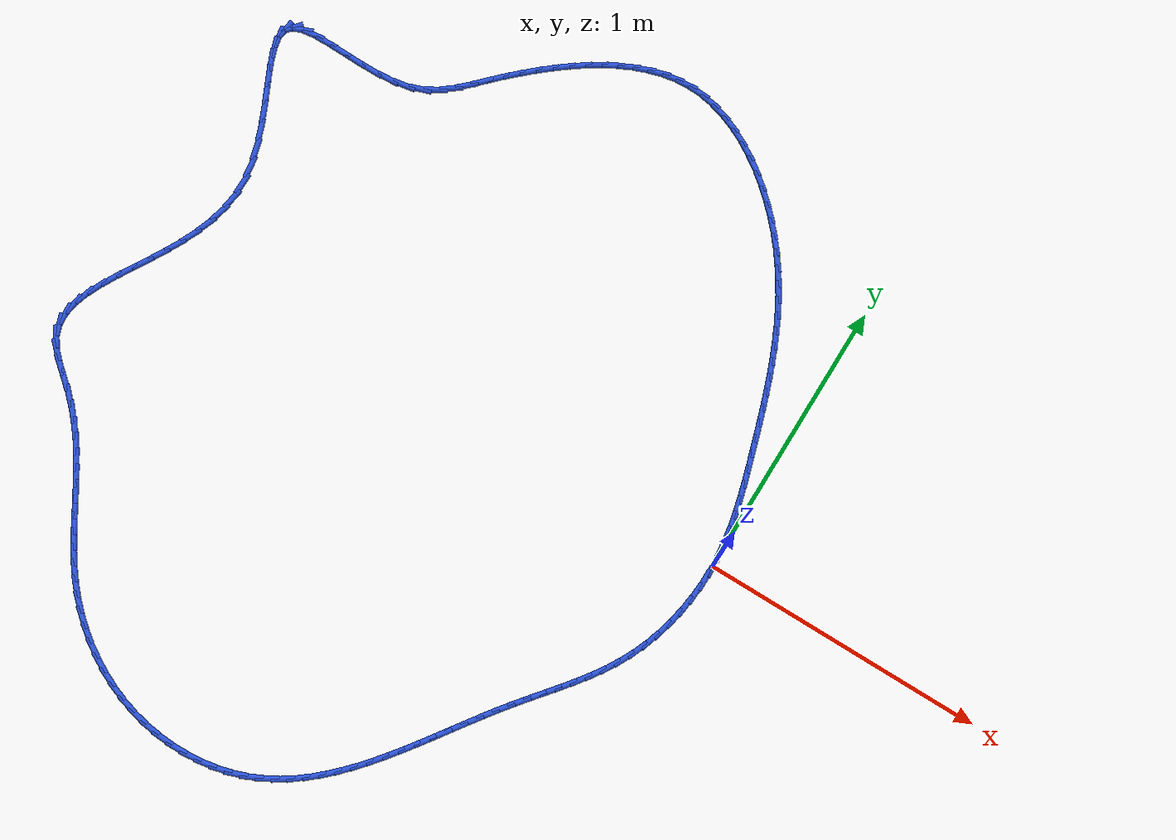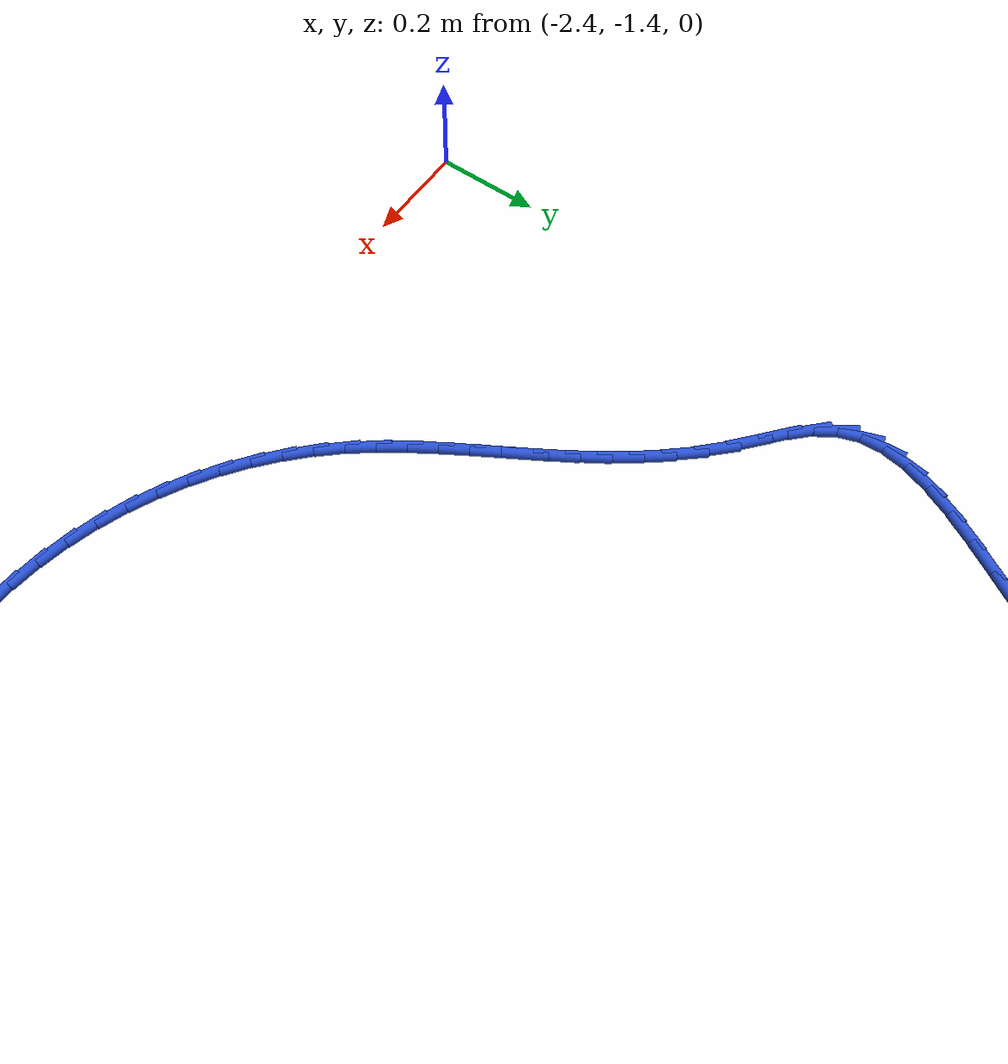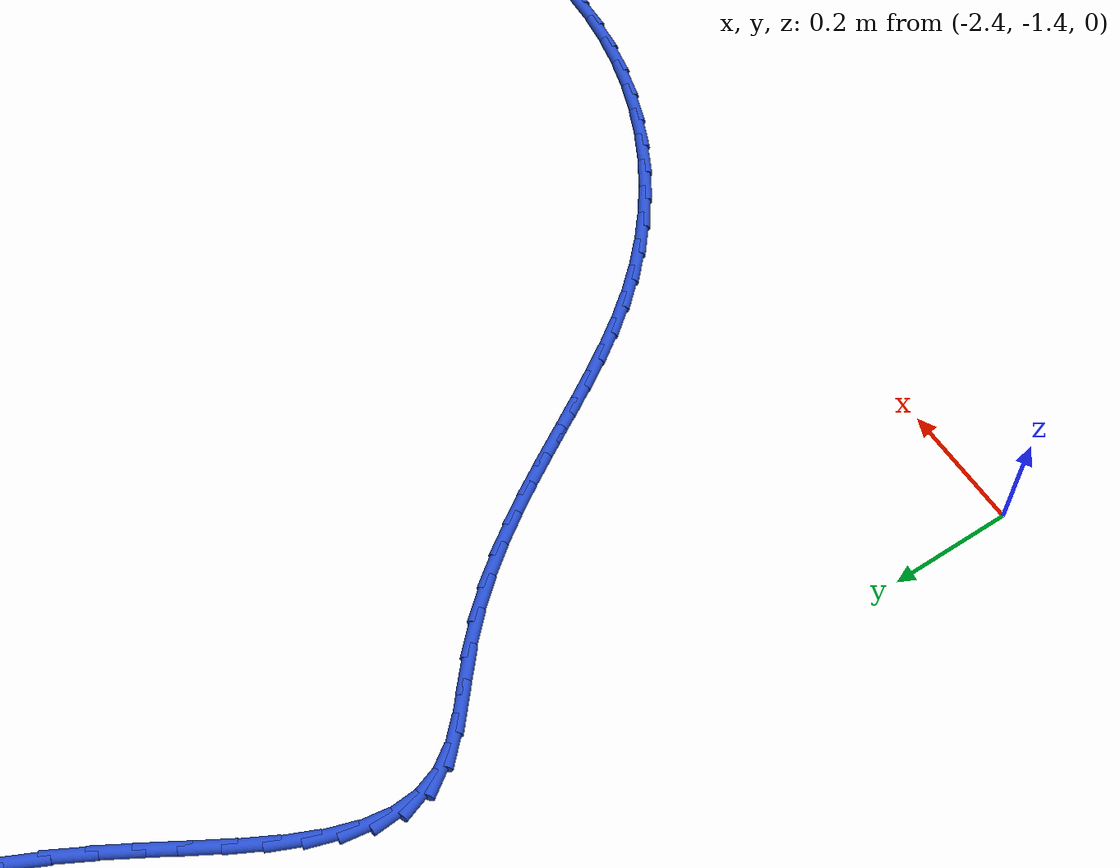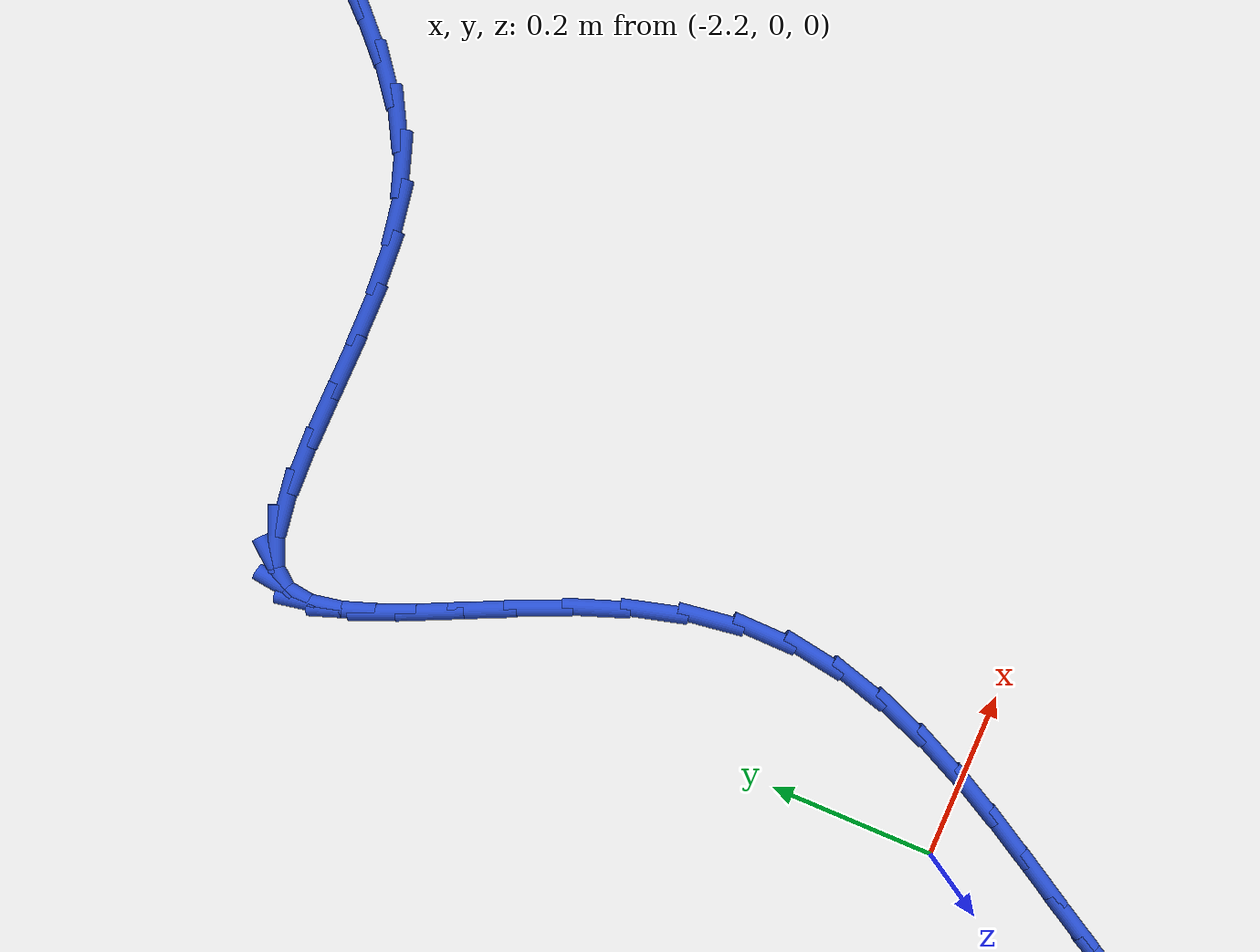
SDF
<sdf version="1.6">
 <world name="default">
  <light name="sun" type="directional">
   <pose>0 0 10 0 -0 0</pose>
   <diffuse>0.8 0.8 0.8 1</diffuse>
   <specular>0.2 0.2 0.2 1</specular>
   <attenuation>
    <range>1000</range>
    <constant>0.9</constant>
    <linear>0.01</linear>
    <quadratic>0.001</quadratic>
   </attenuation>
   <direction>-0.5 0.1 -0.9</direction>
  </light>
  <model name="ground_plane">
   <static>1</static>
   <link name="link">
    <collision name="collision">
     <geometry><plane><normal>0 0 1</normal><size>100 100</size></plane></geometry>
     <surface><friction><ode><mu>100</mu><mu2>50</mu2></ode></friction></surface>
    </collision>
    <visual name="visual">
     <cast_shadows>0</cast_shadows>
     <geometry><plane><normal>0 0 1</normal><size>100 100</size></plane></geometry>
     <material>
      <script><uri>file://media/materials/scripts/gazebo.material</uri><name>Gazebo/WhiteGlow</name></script>
     </material>
    </visual>
   </link>
  </model>
  <gravity>0 0 -9.8</gravity>
  <magnetic_field>6e-06 2.3e-05 -4.2e-05</magnetic_field>
  <atmosphere type="adiabatic"/>
  <physics name="default_physics" default="0" type="ode">
   <max_step_size>0.001</max_step_size>
   <real_time_factor>1</real_time_factor>
   <real_time_update_rate>1000</real_time_update_rate>
  </physics>
  <scene><ambient>0.4 0.4 0.4 1</ambient><background>0.7 0.7 0.7 1</background><shadows>1</shadows></scene>
  <spherical_coordinates>
   <surface_model>EARTH_WGS84</surface_model>
   <latitude_deg>0</latitude_deg>
   <longitude_deg>0</longitude_deg>
   <elevation>0</elevation>
   <heading_deg>0</heading_deg>
  </spherical_coordinates>
  <model name="line">
   <link name="link_0">
    <pose>3.2959746043559335e-17 6.938893903907228e-17 0.01 0 1.57 -1.501933321080894</pose>
    <collision name="collision">
     <geometry><cylinder><radius>0.01</radius><length>0.08</length></cylinder></geometry>
    </collision>
    <visual name="visual">
     <material>
      <script><name>Gazebo/Blue</name><uri>file://media/materials/scripts/gazebo.material</uri></script>
     </material>
     <geometry><cylinder><radius>0.01</radius><length>0.08</length></cylinder></geometry>
    </visual>
   </link>
   <link name="link_1">
    <pose>-0.0036937516715437836 0.053554314927913765 0.01 0 1.57 -1.4448695262906772</pose>
    <collision name="collision">
     <geometry><cylinder><radius>0.01</radius><length>0.08</length></cylinder></geometry>
    </collision>
    <visual name="visual">
     <material>
      <script><name>Gazebo/Blue</name><uri>file://media/materials/scripts/gazebo.material</uri></script>
     </material>
     <geometry><cylinder><radius>0.01</radius><length>0.08</length></cylinder></geometry>
    </visual>
   </link>
   <link name="link_2">
    <pose>-0.010414687617261727 0.10664366862864294 0.01 0 1.57 -1.3957806114475053</pose>
    <collision name="collision">
     <geometry><cylinder><radius>0.01</radius><length>0.08</length></cylinder></geometry>
    </collision>
    <visual name="visual">
     <material>
      <script><name>Gazebo/Blue</name><uri>file://media/materials/scripts/gazebo.material</uri></script>
     </material>
     <geometry><cylinder><radius>0.01</radius><length>0.08</length></cylinder></geometry>
    </visual>
   </link>
   <link name="link_3">
    <pose>-0.019729100022731504 0.15931960069034995 0.01 0 1.57 -1.354882618912627</pose>
    <collision name="collision">
     <geometry><cylinder><radius>0.01</radius><length>0.08</length></cylinder></geometry>
    </collision>
    <visual name="visual">
     <material>
      <script><name>Gazebo/Blue</name><uri>file://media/materials/scripts/gazebo.material</uri></script>
     </material>
     <geometry><cylinder><radius>0.01</radius><length>0.08</length></cylinder></geometry>
    </visual>
   </link>
   <link name="link_4">
    <pose>-0.031203281073530816 0.21163365070119713 0.01 0 1.57 -1.3222136753891178</pose>
    <collision name="collision">
     <geometry><cylinder><radius>0.01</radius><length>0.08</length></cylinder></geometry>
    </collision>
    <visual name="visual">
     <material>
      <script><name>Gazebo/Blue</name><uri>file://media/materials/scripts/gazebo.material</uri></script>
     </material>
     <geometry><cylinder><radius>0.01</radius><length>0.08</length></cylinder></geometry>
    </visual>
   </link>
   <link name="link_5">
    <pose>-0.04440352295523738 0.26363735824934675 0.01 0 1.57 -1.2977155558671318</pose>
    <collision name="collision">
     <geometry><cylinder><radius>0.01</radius><length>0.08</length></cylinder></geometry>
    </collision>
    <visual name="visual">
     <material>
      <script><name>Gazebo/Blue</name><uri>file://media/materials/scripts/gazebo.material</uri></script>
     </material>
     <geometry><cylinder><radius>0.01</radius><length>0.08</length></cylinder></geometry>
    </visual>
   </link>
   <link name="link_6">
    <pose>-0.05889611785342893 0.3153822629229612 0.01 0 1.57 -1.281299743717585</pose>
    <collision name="collision">
     <geometry><cylinder><radius>0.01</radius><length>0.08</length></cylinder></geometry>
    </collision>
    <visual name="visual">
     <material>
      <script><name>Gazebo/Blue</name><uri>file://media/materials/scripts/gazebo.material</uri></script>
     </material>
     <geometry><cylinder><radius>0.01</radius><length>0.08</length></cylinder></geometry>
    </visual>
   </link>
   <link name="link_7">
    <pose>-0.07424735795368313 0.3669199043102027 0.01 0 1.57 -1.2728729128299205</pose>
    <collision name="collision">
     <geometry><cylinder><radius>0.01</radius><length>0.08</length></cylinder></geometry>
    </collision>
    <visual name="visual">
     <material>
      <script><name>Gazebo/Blue</name><uri>file://media/materials/scripts/gazebo.material</uri></script>
     </material>
     <geometry><cylinder><radius>0.01</radius><length>0.08</length></cylinder></geometry>
    </visual>
   </link>
   <link name="link_8">
    <pose>-0.09002474386038198 0.418301594653843 0.01 0 1.57 -1.2688423150533645</pose>
    <collision name="collision">
     <geometry><cylinder><radius>0.01</radius><length>0.08</length></cylinder></geometry>
    </collision>
    <visual name="visual">
     <material>
      <script><name>Gazebo/Blue</name><uri>file://media/materials/scripts/gazebo.material</uri></script>
     </material>
     <geometry><cylinder><radius>0.01</radius><length>0.08</length></cylinder></geometry>
    </visual>
   </link>
   <link name="link_9">
    <pose>-0.10598533659779288 0.46954298332251443 0.01 0 1.57 -1.2617801475753552</pose>
    <collision name="collision">
     <geometry><cylinder><radius>0.01</radius><length>0.08</length></cylinder></geometry>
    </collision>
    <visual name="visual">
     <material>
      <script><name>Gazebo/Blue</name><uri>file://media/materials/scripts/gazebo.material</uri></script>
     </material>
     <geometry><cylinder><radius>0.01</radius><length>0.08</length></cylinder></geometry>
    </visual>
   </link>
   <link name="link_10">
    <pose>-0.1222803289394932 0.5205855698650784 0.01 0 1.57 -1.2507417529395524</pose>
    <collision name="collision">
     <geometry><cylinder><radius>0.01</radius><length>0.08</length></cylinder></geometry>
    </collision>
    <visual name="visual">
     <material>
      <script><name>Gazebo/Blue</name><uri>file://media/materials/scripts/gazebo.material</uri></script>
     </material>
     <geometry><cylinder><radius>0.01</radius><length>0.08</length></cylinder></geometry>
    </visual>
   </link>
   <link name="link_11">
    <pose>-0.13911004619218892 0.5713616103008354 0.01 0 1.57 -1.2357091730468477</pose>
    <collision name="collision">
     <geometry><cylinder><radius>0.01</radius><length>0.08</length></cylinder></geometry>
    </collision>
    <visual name="visual">
     <material>
      <script><name>Gazebo/Blue</name><uri>file://media/materials/scripts/gazebo.material</uri></script>
     </material>
     <geometry><cylinder><radius>0.01</radius><length>0.08</length></cylinder></geometry>
    </visual>
   </link>
   <link name="link_12">
    <pose>-0.15667481366258565 0.6218033606490847 0.01 0 1.57 -1.216672223572653</pose>
    <collision name="collision">
     <geometry><cylinder><radius>0.01</radius><length>0.08</length></cylinder></geometry>
    </collision>
    <visual name="visual">
     <material>
      <script><name>Gazebo/Blue</name><uri>file://media/materials/scripts/gazebo.material</uri></script>
     </material>
     <geometry><cylinder><radius>0.01</radius><length>0.08</length></cylinder></geometry>
    </visual>
   </link>
   <link name="link_13">
    <pose>-0.1751749566573893 0.6718430769291257 0.01 0 1.57 -1.1936357602661762</pose>
    <collision name="collision">
     <geometry><cylinder><radius>0.01</radius><length>0.08</length></cylinder></geometry>
    </collision>
    <visual name="visual">
     <material>
      <script><name>Gazebo/Blue</name><uri>file://media/materials/scripts/gazebo.material</uri></script>
     </material>
     <geometry><cylinder><radius>0.01</radius><length>0.08</length></cylinder></geometry>
    </visual>
   </link>
   <link name="link_14">
    <pose>-0.19481080048330557 0.7214130151602582 0.01 0 1.57 -1.1666288153397435</pose>
    <collision name="collision">
     <geometry><cylinder><radius>0.01</radius><length>0.08</length></cylinder></geometry>
    </collision>
    <visual name="visual">
     <material>
      <script><name>Gazebo/Blue</name><uri>file://media/materials/scripts/gazebo.material</uri></script>
     </material>
     <geometry><cylinder><radius>0.01</radius><length>0.08</length></cylinder></geometry>
    </visual>
   </link>
   <link name="link_15">
    <pose>-0.2157826704470402 0.7704454313617817 0.01 0 1.57 -1.1357153022135817</pose>
    <collision name="collision">
     <geometry><cylinder><radius>0.01</radius><length>0.08</length></cylinder></geometry>
    </collision>
    <visual name="visual">
     <material>
      <script><name>Gazebo/Blue</name><uri>file://media/materials/scripts/gazebo.material</uri></script>
     </material>
     <geometry><cylinder><radius>0.01</radius><length>0.08</length></cylinder></geometry>
    </visual>
   </link>
   <link name="link_16">
    <pose>-0.2382908918552991 0.8188725815529957 0.01 0 1.57 -1.1010056919985685</pose>
    <collision name="collision">
     <geometry><cylinder><radius>0.01</radius><length>0.08</length></cylinder></geometry>
    </collision>
    <visual name="visual">
     <material>
      <script><name>Gazebo/Blue</name><uri>file://media/materials/scripts/gazebo.material</uri></script>
     </material>
     <geometry><cylinder><radius>0.01</radius><length>0.08</length></cylinder></geometry>
    </visual>
   </link>
   <link name="link_17">
    <pose>-0.262535790014788 0.8666267217532001 0.01 0 1.57 -1.0626686892570967</pose>
    <collision name="collision">
     <geometry><cylinder><radius>0.01</radius><length>0.08</length></cylinder></geometry>
    </collision>
    <visual name="visual">
     <material>
      <script><name>Gazebo/Blue</name><uri>file://media/materials/scripts/gazebo.material</uri></script>
     </material>
     <geometry><cylinder><radius>0.01</radius><length>0.08</length></cylinder></geometry>
    </visual>
   </link>
   <link name="link_18">
    <pose>-0.2887176902322126 0.9136401079816943 0.01 0 1.57 -1.020941531363911</pose>
    <collision name="collision">
     <geometry><cylinder><radius>0.01</radius><length>0.08</length></cylinder></geometry>
    </collision>
    <visual name="visual">
     <material>
      <script><name>Gazebo/Blue</name><uri>file://media/materials/scripts/gazebo.material</uri></script>
     </material>
     <geometry><cylinder><radius>0.01</radius><length>0.08</length></cylinder></geometry>
    </visual>
   </link>
   <link name="link_19">
    <pose>-0.3170369178142788 0.9598449962577779 0.01 0 1.57 -0.9761372068941707</pose>
    <collision name="collision">
     <geometry><cylinder><radius>0.01</radius><length>0.08</length></cylinder></geometry>
    </collision>
    <visual name="visual">
     <material>
      <script><name>Gazebo/Blue</name><uri>file://media/materials/scripts/gazebo.material</uri></script>
     </material>
     <geometry><cylinder><radius>0.01</radius><length>0.08</length></cylinder></geometry>
    </visual>
   </link>
   <link name="link_20">
    <pose>-0.3476937980676922 1.0051736426007503 0.01 0 1.57 -0.9286467761222325</pose>
    <collision name="collision">
     <geometry><cylinder><radius>0.01</radius><length>0.08</length></cylinder></geometry>
    </collision>
    <visual name="visual">
     <material>
      <script><name>Gazebo/Blue</name><uri>file://media/materials/scripts/gazebo.material</uri></script>
     </material>
     <geometry><cylinder><radius>0.01</radius><length>0.08</length></cylinder></geometry>
    </visual>
   </link>
   <link name="link_21">
    <pose>-0.3808886562991589 1.0495583030299114 0.01 0 1.57 -0.8790103083002485</pose>
    <collision name="collision">
     <geometry><cylinder><radius>0.01</radius><length>0.08</length></cylinder></geometry>
    </collision>
    <visual name="visual">
     <material>
      <script><name>Gazebo/Blue</name><uri>file://media/materials/scripts/gazebo.material</uri></script>
     </material>
     <geometry><cylinder><radius>0.01</radius><length>0.08</length></cylinder></geometry>
    </visual>
   </link>
   <link name="link_22">
    <pose>-0.4167998213265273 1.0929113079216437 0.01 0 1.57 -0.8282399786854006</pose>
    <collision name="collision">
     <geometry><cylinder><radius>0.01</radius><length>0.08</length></cylinder></geometry>
    </collision>
    <visual name="visual">
     <material>
      <script><name>Gazebo/Blue</name><uri>file://media/materials/scripts/gazebo.material</uri></script>
     </material>
     <geometry><cylinder><radius>0.01</radius><length>0.08</length></cylinder></geometry>
    </visual>
   </link>
   <link name="link_23">
    <pose>-0.45534331640955483 1.1349073766899804 0.01 0 1.57 -0.7760028842874098</pose>
    <collision name="collision">
     <geometry><cylinder><radius>0.01</radius><length>0.08</length></cylinder></geometry>
    </collision>
    <visual name="visual">
     <material>
      <script><name>Gazebo/Blue</name><uri>file://media/materials/scripts/gazebo.material</uri></script>
     </material>
     <geometry><cylinder><radius>0.01</radius><length>0.08</length></cylinder></geometry>
    </visual>
   </link>
   <link name="link_24">
    <pose>-0.4962627496123914 1.1750650454760951 0.01 0 1.57 -0.7211756866059735</pose>
    <collision name="collision">
     <geometry><cylinder><radius>0.01</radius><length>0.08</length></cylinder></geometry>
    </collision>
    <visual name="visual">
     <material>
      <script><name>Gazebo/Blue</name><uri>file://media/materials/scripts/gazebo.material</uri></script>
     </material>
     <geometry><cylinder><radius>0.01</radius><length>0.08</length></cylinder></geometry>
    </visual>
   </link>
   <link name="link_25">
    <pose>-0.5392987088314697 1.21290011458528 0.01 0 1.57 -0.6625879316467792</pose>
    <collision name="collision">
     <geometry><cylinder><radius>0.01</radius><length>0.08</length></cylinder></geometry>
    </collision>
    <visual name="visual">
     <material>
      <script><name>Gazebo/Blue</name><uri>file://media/materials/scripts/gazebo.material</uri></script>
     </material>
     <geometry><cylinder><radius>0.01</radius><length>0.08</length></cylinder></geometry>
    </visual>
   </link>
   <link name="link_26">
    <pose>-0.5841917819632219 1.2479283843228262 0.01 0 1.57 -0.5989915505566049</pose>
    <collision name="collision">
     <geometry><cylinder><radius>0.01</radius><length>0.08</length></cylinder></geometry>
    </collision>
    <visual name="visual">
     <material>
      <script><name>Gazebo/Blue</name><uri>file://media/materials/scripts/gazebo.material</uri></script>
     </material>
     <geometry><cylinder><radius>0.01</radius><length>0.08</length></cylinder></geometry>
    </visual>
   </link>
   <link name="link_27">
    <pose>-0.6306825569040805 1.279665654994026 0.01 0 1.57 -0.5290377149903359</pose>
    <collision name="collision">
     <geometry><cylinder><radius>0.01</radius><length>0.08</length></cylinder></geometry>
    </collision>
    <visual name="visual">
     <material>
      <script><name>Gazebo/Blue</name><uri>file://media/materials/scripts/gazebo.material</uri></script>
     </material>
     <geometry><cylinder><radius>0.01</radius><length>0.08</length></cylinder></geometry>
    </visual>
   </link>
   <link name="link_28">
    <pose>-0.6785116215504776 1.30762772690417 0.01 0 1.57 -0.45128308796626326</pose>
    <collision name="collision">
     <geometry><cylinder><radius>0.01</radius><length>0.08</length></cylinder></geometry>
    </collision>
    <visual name="visual">
     <material>
      <script><name>Gazebo/Blue</name><uri>file://media/materials/scripts/gazebo.material</uri></script>
     </material>
     <geometry><cylinder><radius>0.01</radius><length>0.08</length></cylinder></geometry>
    </visual>
   </link>
   <link name="link_29">
    <pose>-0.7274195637988462 1.3313304003585522 0.01 0 1.57 -0.3642476298598525</pose>
    <collision name="collision">
     <geometry><cylinder><radius>0.01</radius><length>0.08</length></cylinder></geometry>
    </collision>
    <visual name="visual">
     <material>
      <script><name>Gazebo/Blue</name><uri>file://media/materials/scripts/gazebo.material</uri></script>
     </material>
     <geometry><cylinder><radius>0.01</radius><length>0.08</length></cylinder></geometry>
    </visual>
   </link>
   <link name="link_30">
    <pose>-0.7771469715456176 1.3502894756624617 0.01 0 1.57 -0.2665577054320206</pose>
    <collision name="collision">
     <geometry><cylinder><radius>0.01</radius><length>0.08</length></cylinder></geometry>
    </collision>
    <visual name="visual">
     <material>
      <script><name>Gazebo/Blue</name><uri>file://media/materials/scripts/gazebo.material</uri></script>
     </material>
     <geometry><cylinder><radius>0.01</radius><length>0.08</length></cylinder></geometry>
    </visual>
   </link>
   <link name="link_31">
    <pose>-0.8274344326872252 1.3640207531211916 0.01 0 1.57 -0.1572129119618295</pose>
    <collision name="collision">
     <geometry><cylinder><radius>0.01</radius><length>0.08</length></cylinder></geometry>
    </collision>
    <visual name="visual">
     <material>
      <script><name>Gazebo/Blue</name><uri>file://media/materials/scripts/gazebo.material</uri></script>
     </material>
     <geometry><cylinder><radius>0.01</radius><length>0.08</length></cylinder></geometry>
    </visual>
   </link>
   <link name="link_32">
    <pose>-0.8780225351201005 1.3720400330400342 0.01 0 1.57 -0.03637510944081978</pose>
    <collision name="collision">
     <geometry><cylinder><radius>0.01</radius><length>0.08</length></cylinder></geometry>
    </collision>
    <visual name="visual">
     <material>
      <script><name>Gazebo/Blue</name><uri>file://media/materials/scripts/gazebo.material</uri></script>
     </material>
     <geometry><cylinder><radius>0.01</radius><length>0.08</length></cylinder></geometry>
    </visual>
   </link>
   <link name="link_33">
    <pose>-0.9286546549691455 1.3738825946733981 0.01 0 1.57 0.08562041745296425</pose>
    <collision name="collision">
     <geometry><cylinder><radius>0.01</radius><length>0.08</length></cylinder></geometry>
    </collision>
    <visual name="visual">
     <material>
      <script><name>Gazebo/Blue</name><uri>file://media/materials/scripts/gazebo.material</uri></script>
     </material>
     <geometry><cylinder><radius>0.01</radius><length>0.08</length></cylinder></geometry>
    </visual>
   </link>
   <link name="link_34">
    <pose>-0.9791408199066888 1.3695493541900734 0.01 0 1.57 0.1971814877515869</pose>
    <collision name="collision">
     <geometry><cylinder><radius>0.01</radius><length>0.08</length></cylinder></geometry>
    </collision>
    <visual name="visual">
     <material>
      <script><name>Gazebo/Blue</name><uri>file://media/materials/scripts/gazebo.material</uri></script>
     </material>
     <geometry><cylinder><radius>0.01</radius><length>0.08</length></cylinder></geometry>
    </visual>
   </link>
   <link name="link_35">
    <pose>-1.0293591412908811 1.3595168697898345 0.01 0 1.57 0.2966806705798629</pose>
    <collision name="collision">
     <geometry><cylinder><radius>0.01</radius><length>0.08</length></cylinder></geometry>
    </collision>
    <visual name="visual">
     <material>
      <script><name>Gazebo/Blue</name><uri>file://media/materials/scripts/gazebo.material</uri></script>
     </material>
     <geometry><cylinder><radius>0.01</radius><length>0.08</length></cylinder></geometry>
    </visual>
   </link>
   <link name="link_36">
    <pose>-1.0791908051766064 1.3442831799284112 0.01 0 1.57 0.384108046037236</pose>
    <collision name="collision">
     <geometry><cylinder><radius>0.01</radius><length>0.08</length></cylinder></geometry>
    </collision>
    <visual name="visual">
     <material>
      <script><name>Gazebo/Blue</name><uri>file://media/materials/scripts/gazebo.material</uri></script>
     </material>
     <geometry><cylinder><radius>0.01</radius><length>0.08</length></cylinder></geometry>
    </visual>
   </link>
   <link name="link_37">
    <pose>-1.1285169976187461 1.3243463230615307 0.01 0 1.57 0.4602091144190262</pose>
    <collision name="collision">
     <geometry><cylinder><radius>0.01</radius><length>0.08</length></cylinder></geometry>
    </collision>
    <visual name="visual">
     <material>
      <script><name>Gazebo/Blue</name><uri>file://media/materials/scripts/gazebo.material</uri></script>
     </material>
     <geometry><cylinder><radius>0.01</radius><length>0.08</length></cylinder></geometry>
    </visual>
   </link>
   <link name="link_38">
    <pose>-1.1772189046721835 1.3002043376449228 0.01 0 1.57 0.5260980093758193</pose>
    <collision name="collision">
     <geometry><cylinder><radius>0.01</radius><length>0.08</length></cylinder></geometry>
    </collision>
    <visual name="visual">
     <material>
      <script><name>Gazebo/Blue</name><uri>file://media/materials/scripts/gazebo.material</uri></script>
     </material>
     <geometry><cylinder><radius>0.01</radius><length>0.08</length></cylinder></geometry>
    </visual>
   </link>
   <link name="link_39">
    <pose>-1.2251777123918008 1.2723552621343155 0.01 0 1.57 0.5829909804828087</pose>
    <collision name="collision">
     <geometry><cylinder><radius>0.01</radius><length>0.08</length></cylinder></geometry>
    </collision>
    <visual name="visual">
     <material>
      <script><name>Gazebo/Blue</name><uri>file://media/materials/scripts/gazebo.material</uri></script>
     </material>
     <geometry><cylinder><radius>0.01</radius><length>0.08</length></cylinder></geometry>
    </visual>
   </link>
   <link name="link_40">
    <pose>-1.2722746068324808 1.2412971349854371 0.01 0 1.57 0.6320521343198325</pose>
    <collision name="collision">
     <geometry><cylinder><radius>0.01</radius><length>0.08</length></cylinder></geometry>
    </collision>
    <visual name="visual">
     <material>
      <script><name>Gazebo/Blue</name><uri>file://media/materials/scripts/gazebo.material</uri></script>
     </material>
     <geometry><cylinder><radius>0.01</radius><length>0.08</length></cylinder></geometry>
    </visual>
   </link>
   <link name="link_41">
    <pose>-1.318390774049107 1.2075279946540167 0.01 0 1.57 0.6743183839804233</pose>
    <collision name="collision">
     <geometry><cylinder><radius>0.01</radius><length>0.08</length></cylinder></geometry>
    </collision>
    <visual name="visual">
     <material>
      <script><name>Gazebo/Blue</name><uri>file://media/materials/scripts/gazebo.material</uri></script>
     </material>
     <geometry><cylinder><radius>0.01</radius><length>0.08</length></cylinder></geometry>
    </visual>
   </link>
   <link name="link_42">
    <pose>-1.3634074000965608 1.1715458795957825 0.01 0 1.57 0.7106716796548233</pose>
    <collision name="collision">
     <geometry><cylinder><radius>0.01</radius><length>0.08</length></cylinder></geometry>
    </collision>
    <visual name="visual">
     <material>
      <script><name>Gazebo/Blue</name><uri>file://media/materials/scripts/gazebo.material</uri></script>
     </material>
     <geometry><cylinder><radius>0.01</radius><length>0.08</length></cylinder></geometry>
    </visual>
   </link>
   <link name="link_43">
    <pose>-1.407205671029725 1.1338488282664636 0.01 0 1.57 0.7418355653986678</pose>
    <collision name="collision">
     <geometry><cylinder><radius>0.01</radius><length>0.08</length></cylinder></geometry>
    </collision>
    <visual name="visual">
     <material>
      <script><name>Gazebo/Blue</name><uri>file://media/materials/scripts/gazebo.material</uri></script>
     </material>
     <geometry><cylinder><radius>0.01</radius><length>0.08</length></cylinder></geometry>
    </visual>
   </link>
   <link name="link_44">
    <pose>-1.4496667729034827 1.0949348791217877 0.01 0 1.57 0.768381630971801</pose>
    <collision name="collision">
     <geometry><cylinder><radius>0.01</radius><length>0.08</length></cylinder></geometry>
    </collision>
    <visual name="visual">
     <material>
      <script><name>Gazebo/Blue</name><uri>file://media/materials/scripts/gazebo.material</uri></script>
     </material>
     <geometry><cylinder><radius>0.01</radius><length>0.08</length></cylinder></geometry>
    </visual>
   </link>
   <link name="link_45">
    <pose>-1.490671891772716 1.0553020706174834 0.01 0 1.57 0.7905040155484132</pose>
    <collision name="collision">
     <geometry><cylinder><radius>0.01</radius><length>0.08</length></cylinder></geometry>
    </collision>
    <visual name="visual">
     <material>
      <script><name>Gazebo/Blue</name><uri>file://media/materials/scripts/gazebo.material</uri></script>
     </material>
     <geometry><cylinder><radius>0.01</radius><length>0.08</length></cylinder></geometry>
    </visual>
   </link>
   <link name="link_46">
    <pose>-1.5301132151105097 1.0154559136096486 0.01 0 1.57 0.792292015695472</pose>
    <collision name="collision">
     <geometry><cylinder><radius>0.01</radius><length>0.08</length></cylinder></geometry>
    </collision>
    <visual name="visual">
     <material>
      <script><name>Gazebo/Blue</name><uri>file://media/materials/scripts/gazebo.material</uri></script>
     </material>
     <geometry><cylinder><radius>0.01</radius><length>0.08</length></cylinder></geometry>
    </visual>
   </link>
   <link name="link_47">
    <pose>-1.568627065127574 0.9764073513073802 0.01 0 1.57 0.7457963131499671</pose>
    <collision name="collision">
     <geometry><cylinder><radius>0.01</radius><length>0.08</length></cylinder></geometry>
    </collision>
    <visual name="visual">
     <material>
      <script><name>Gazebo/Blue</name><uri>file://media/materials/scripts/gazebo.material</uri></script>
     </material>
     <geometry><cylinder><radius>0.01</radius><length>0.08</length></cylinder></geometry>
    </visual>
   </link>
   <link name="link_48">
    <pose>-1.6080542875060642 0.9399854652240793 0.01 0 1.57 0.646115199430709</pose>
    <collision name="collision">
     <geometry><cylinder><radius>0.01</radius><length>0.08</length></cylinder></geometry>
    </collision>
    <visual name="visual">
     <material>
      <script><name>Gazebo/Blue</name><uri>file://media/materials/scripts/gazebo.material</uri></script>
     </material>
     <geometry><cylinder><radius>0.01</radius><length>0.08</length></cylinder></geometry>
    </visual>
   </link>
   <link name="link_49">
    <pose>-1.650345556188455 0.9080939345948116 0.01 0 1.57 0.4954662282466812</pose>
    <collision name="collision">
     <geometry><cylinder><radius>0.01</radius><length>0.08</length></cylinder></geometry>
    </collision>
    <visual name="visual">
     <material>
      <script><name>Gazebo/Blue</name><uri>file://media/materials/scripts/gazebo.material</uri></script>
     </material>
     <geometry><cylinder><radius>0.01</radius><length>0.08</length></cylinder></geometry>
    </visual>
   </link>
   <link name="link_50">
    <pose>-1.6974515451172223 0.882636438654644 0.01 0 1.57 0.3108237156759533</pose>
    <collision name="collision">
     <geometry><cylinder><radius>0.01</radius><length>0.08</length></cylinder></geometry>
    </collision>
    <visual name="visual">
     <material>
      <script><name>Gazebo/Blue</name><uri>file://media/materials/scripts/gazebo.material</uri></script>
     </material>
     <geometry><cylinder><radius>0.01</radius><length>0.08</length></cylinder></geometry>
    </visual>
   </link>
   <link name="link_51">
    <pose>-1.7511698642561189 0.8653801816602584 0.01 0 1.57 0.1563179266628314</pose>
    <collision name="collision">
     <geometry><cylinder><radius>0.01</radius><length>0.08</length></cylinder></geometry>
    </collision>
    <visual name="visual">
     <material>
      <script><name>Gazebo/Blue</name><uri>file://media/materials/scripts/gazebo.material</uri></script>
     </material>
     <geometry><cylinder><radius>0.01</radius><length>0.08</length></cylinder></geometry>
    </visual>
   </link>
   <link name="link_52">
    <pose>-1.810911759417487 0.8559646367149714 0.01 0 1.57 0.05710769198709494</pose>
    <collision name="collision">
     <geometry><cylinder><radius>0.01</radius><length>0.08</length></cylinder></geometry>
    </collision>
    <visual name="visual">
     <material>
      <script><name>Gazebo/Blue</name><uri>file://media/materials/scripts/gazebo.material</uri></script>
     </material>
     <geometry><cylinder><radius>0.01</radius><length>0.08</length></cylinder></geometry>
    </visual>
   </link>
   <link name="link_53">
    <pose>-1.874201037666298 0.852346397877645 0.01 0 1.57 -0.0013947347581650356</pose>
    <collision name="collision">
     <geometry><cylinder><radius>0.01</radius><length>0.08</length></cylinder></geometry>
    </collision>
    <visual name="visual">
     <material>
      <script><name>Gazebo/Blue</name><uri>file://media/materials/scripts/gazebo.material</uri></script>
     </material>
     <geometry><cylinder><radius>0.01</radius><length>0.08</length></cylinder></geometry>
    </visual>
   </link>
   <link name="link_54">
    <pose>-1.9385099511791346 0.8524360918127413 0.01 0 1.57 -0.02719443414131565</pose>
    <collision name="collision">
     <geometry><cylinder><radius>0.01</radius><length>0.08</length></cylinder></geometry>
    </collision>
    <visual name="visual">
     <material>
      <script><name>Gazebo/Blue</name><uri>file://media/materials/scripts/gazebo.material</uri></script>
     </material>
     <geometry><cylinder><radius>0.01</radius><length>0.08</length></cylinder></geometry>
    </visual>
   </link>
   <link name="link_55">
    <pose>-2.001310752132578 0.8541443451847206 0.01 0 1.57 -0.02105433290349972</pose>
    <collision name="collision">
     <geometry><cylinder><radius>0.01</radius><length>0.08</length></cylinder></geometry>
    </collision>
    <visual name="visual">
     <material>
      <script><name>Gazebo/Blue</name><uri>file://media/materials/scripts/gazebo.material</uri></script>
     </material>
     <geometry><cylinder><radius>0.01</radius><length>0.08</length></cylinder></geometry>
    </visual>
   </link>
   <link name="link_56">
    <pose>-2.060075692703211 0.8553817846580446 0.01 0 1.57 0.02533392742197978</pose>
    <collision name="collision">
     <geometry><cylinder><radius>0.01</radius><length>0.08</length></cylinder></geometry>
    </collision>
    <visual name="visual">
     <material>
      <script><name>Gazebo/Blue</name><uri>file://media/materials/scripts/gazebo.material</uri></script>
     </material>
     <geometry><cylinder><radius>0.01</radius><length>0.08</length></cylinder></geometry>
    </visual>
   </link>
   <link name="link_57">
    <pose>-2.1122770250676153 0.8540590368971739 0.01 0 1.57 0.1376603575818182</pose>
    <collision name="collision">
     <geometry><cylinder><radius>0.01</radius><length>0.08</length></cylinder></geometry>
    </collision>
    <visual name="visual">
     <material>
      <script><name>Gazebo/Blue</name><uri>file://media/materials/scripts/gazebo.material</uri></script>
     </material>
     <geometry><cylinder><radius>0.01</radius><length>0.08</length></cylinder></geometry>
    </visual>
   </link>
   <link name="link_58">
    <pose>-2.1553870014023744 0.8480867285665699 0.01 0 1.57 0.3836476404065954</pose>
    <collision name="collision">
     <geometry><cylinder><radius>0.01</radius><length>0.08</length></cylinder></geometry>
    </collision>
    <visual name="visual">
     <material>
      <script><name>Gazebo/Blue</name><uri>file://media/materials/scripts/gazebo.material</uri></script>
     </material>
     <geometry><cylinder><radius>0.01</radius><length>0.08</length></cylinder></geometry>
    </visual>
   </link>
   <link name="link_59">
    <pose>-2.186877873884069 0.8353754863306935 0.01 0 1.57 0.8834295352332672</pose>
    <collision name="collision">
     <geometry><cylinder><radius>0.01</radius><length>0.08</length></cylinder></geometry>
    </collision>
    <visual name="visual">
     <material>
      <script><name>Gazebo/Blue</name><uri>file://media/materials/scripts/gazebo.material</uri></script>
     </material>
     <geometry><cylinder><radius>0.01</radius><length>0.08</length></cylinder></geometry>
    </visual>
   </link>
   <link name="link_60">
    <pose>-2.2044445000141977 0.8139767485254239 0.01 0 1.57 1.4354986765860624</pose>
    <collision name="collision">
     <geometry><cylinder><radius>0.01</radius><length>0.08</length></cylinder></geometry>
    </collision>
    <visual name="visual">
     <material>
      <script><name>Gazebo/Blue</name><uri>file://media/materials/scripts/gazebo.material</uri></script>
     </material>
     <geometry><cylinder><radius>0.01</radius><length>0.08</length></cylinder></geometry>
    </visual>
   </link>
   <link name="link_61">
    <pose>-2.2085656508752325 0.7837029514527365 0.01 0 1.57 -1.3904993530874334</pose>
    <collision name="collision">
     <geometry><cylinder><radius>0.01</radius><length>0.08</length></cylinder></geometry>
    </collision>
    <visual name="visual">
     <material>
      <script><name>Gazebo/Blue</name><uri>file://media/materials/scripts/gazebo.material</uri></script>
     </material>
     <geometry><cylinder><radius>0.01</radius><length>0.08</length></cylinder></geometry>
    </visual>
   </link>
   <link name="link_62">
    <pose>-2.2016139103861283 0.745564485466059 0.01 0 1.57 -1.2365730576389933</pose>
    <collision name="collision">
     <geometry><cylinder><radius>0.01</radius><length>0.08</length></cylinder></geometry>
    </collision>
    <visual name="visual">
     <material>
      <script><name>Gazebo/Blue</name><uri>file://media/materials/scripts/gazebo.material</uri></script>
     </material>
     <geometry><cylinder><radius>0.01</radius><length>0.08</length></cylinder></geometry>
    </visual>
   </link>
   <link name="link_63">
    <pose>-2.1859981226895107 0.7005946777587299 0.01 0 1.57 -1.164019764222039</pose>
    <collision name="collision">
     <geometry><cylinder><radius>0.01</radius><length>0.08</length></cylinder></geometry>
    </collision>
    <visual name="visual">
     <material>
      <script><name>Gazebo/Blue</name><uri>file://media/materials/scripts/gazebo.material</uri></script>
     </material>
     <geometry><cylinder><radius>0.01</radius><length>0.08</length></cylinder></geometry>
    </visual>
   </link>
   <link name="link_64">
    <pose>-2.1641271319280047 0.6498268555240855 0.01 0 1.57 -1.1370983738980522</pose>
    <collision name="collision">
     <geometry><cylinder><radius>0.01</radius><length>0.08</length></cylinder></geometry>
    </collision>
    <visual name="visual">
     <material>
      <script><name>Gazebo/Blue</name><uri>file://media/materials/scripts/gazebo.material</uri></script>
     </material>
     <geometry><cylinder><radius>0.01</radius><length>0.08</length></cylinder></geometry>
    </visual>
   </link>
   <link name="link_65">
    <pose>-2.1384097822442314 0.5942943459554636 0.01 0 1.57 -1.1411420173385465</pose>
    <collision name="collision">
     <geometry><cylinder><radius>0.01</radius><length>0.08</length></cylinder></geometry>
    </collision>
    <visual name="visual">
     <material>
      <script><name>Gazebo/Blue</name><uri>file://media/materials/scripts/gazebo.material</uri></script>
     </material>
     <geometry><cylinder><radius>0.01</radius><length>0.08</length></cylinder></geometry>
    </visual>
   </link>
   <link name="link_66">
    <pose>-2.1112549177808155 0.5350304762462009 0.01 0 1.57 -1.1709816858126694</pose>
    <collision name="collision">
     <geometry><cylinder><radius>0.01</radius><length>0.08</length></cylinder></geometry>
    </collision>
    <visual name="visual">
     <material>
      <script><name>Gazebo/Blue</name><uri>file://media/materials/scripts/gazebo.material</uri></script>
     </material>
     <geometry><cylinder><radius>0.01</radius><length>0.08</length></cylinder></geometry>
    </visual>
   </link>
   <link name="link_67">
    <pose>-2.0850713826803826 0.47306857358963494 0.01 0 1.57 -1.2266636765283134</pose>
    <collision name="collision">
     <geometry><cylinder><radius>0.01</radius><length>0.08</length></cylinder></geometry>
    </collision>
    <visual name="visual">
     <material>
      <script><name>Gazebo/Blue</name><uri>file://media/materials/scripts/gazebo.material</uri></script>
     </material>
     <geometry><cylinder><radius>0.01</radius><length>0.08</length></cylinder></geometry>
    </visual>
   </link>
   <link name="link_68">
    <pose>-2.062268021085555 0.40944196517910336 0.01 0 1.57 -1.31195451161064</pose>
    <collision name="collision">
     <geometry><cylinder><radius>0.01</radius><length>0.08</length></cylinder></geometry>
    </collision>
    <visual name="visual">
     <material>
      <script><name>Gazebo/Blue</name><uri>file://media/materials/scripts/gazebo.material</uri></script>
     </material>
     <geometry><cylinder><radius>0.01</radius><length>0.08</length></cylinder></geometry>
    </visual>
   </link>
   <link name="link_69">
    <pose>-2.0452536771389567 0.3451839782079431 0.01 0 1.57 -1.433593073637518</pose>
    <collision name="collision">
     <geometry><cylinder><radius>0.01</radius><length>0.08</length></cylinder></geometry>
    </collision>
    <visual name="visual">
     <material>
      <script><name>Gazebo/Blue</name><uri>file://media/materials/scripts/gazebo.material</uri></script>
     </material>
     <geometry><cylinder><radius>0.01</radius><length>0.08</length></cylinder></geometry>
    </visual>
   </link>
   <link name="link_70">
    <pose>-2.036437021639205 0.28132789596863134 0.01 0 1.57 1.5548215247816843</pose>
    <collision name="collision">
     <geometry><cylinder><radius>0.01</radius><length>0.08</length></cylinder></geometry>
    </collision>
    <visual name="visual">
     <material>
      <script><name>Gazebo/Blue</name><uri>file://media/materials/scripts/gazebo.material</uri></script>
     </material>
     <geometry><cylinder><radius>0.01</radius><length>0.08</length></cylinder></geometry>
    </visual>
   </link>
   <link name="link_71">
    <pose>-2.0374374613391137 0.21870711384787903 0.01 0 1.57 1.4115544534157227</pose>
    <collision name="collision">
     <geometry><cylinder><radius>0.01</radius><length>0.08</length></cylinder></geometry>
    </collision>
    <visual name="visual">
     <material>
      <script><name>Gazebo/Blue</name><uri>file://media/materials/scripts/gazebo.material</uri></script>
     </material>
     <geometry><cylinder><radius>0.01</radius><length>0.08</length></cylinder></geometry>
    </visual>
   </link>
   <link name="link_72">
    <pose>-2.047268231275306 0.15749499183716528 0.01 0 1.57 1.291551451877342</pose>
    <collision name="collision">
     <geometry><cylinder><radius>0.01</radius><length>0.08</length></cylinder></geometry>
    </collision>
    <visual name="visual">
     <material>
      <script><name>Gazebo/Blue</name><uri>file://media/materials/scripts/gazebo.material</uri></script>
     </material>
     <geometry><cylinder><radius>0.01</radius><length>0.08</length></cylinder></geometry>
    </visual>
   </link>
   <link name="link_73">
    <pose>-2.0644053929333523 0.09772884610749549 0.01 0 1.57 1.1961241661566702</pose>
    <collision name="collision">
     <geometry><cylinder><radius>0.01</radius><length>0.08</length></cylinder></geometry>
    </collision>
    <visual name="visual">
     <material>
      <script><name>Gazebo/Blue</name><uri>file://media/materials/scripts/gazebo.material</uri></script>
     </material>
     <geometry><cylinder><radius>0.01</radius><length>0.08</length></cylinder></geometry>
    </visual>
   </link>
   <link name="link_74">
    <pose>-2.0873250077988246 0.039445992829875876 0.01 0 1.57 1.12424684356039</pose>
    <collision name="collision">
     <geometry><cylinder><radius>0.01</radius><length>0.08</length></cylinder></geometry>
    </collision>
    <visual name="visual">
     <material>
      <script><name>Gazebo/Blue</name><uri>file://media/materials/scripts/gazebo.material</uri></script>
     </material>
     <geometry><cylinder><radius>0.01</radius><length>0.08</length></cylinder></geometry>
    </visual>
   </link>
   <link name="link_75">
    <pose>-2.1145031373572953 -0.017316251824687486 0.01 0 1.57 1.0742284082468219</pose>
    <collision name="collision">
     <geometry><cylinder><radius>0.01</radius><length>0.08</length></cylinder></geometry>
    </collision>
    <visual name="visual">
     <material>
      <script><name>Gazebo/Blue</name><uri>file://media/materials/scripts/gazebo.material</uri></script>
     </material>
     <geometry><cylinder><radius>0.01</radius><length>0.08</length></cylinder></geometry>
    </visual>
   </link>
   <link name="link_76">
    <pose>-2.144415843094335 -0.07252057168518905 0.01 0 1.57 1.0447928098181314</pose>
    <collision name="collision">
     <geometry><cylinder><radius>0.01</radius><length>0.08</length></cylinder></geometry>
    </collision>
    <visual name="visual">
     <material>
      <script><name>Gazebo/Blue</name><uri>file://media/materials/scripts/gazebo.material</uri></script>
     </material>
     <geometry><cylinder><radius>0.01</radius><length>0.08</length></cylinder></geometry>
    </visual>
   </link>
   <link name="link_77">
    <pose>-2.175539186495517 -0.12612965058062217 0.01 0 1.57 1.0357111062813753</pose>
    <collision name="collision">
     <geometry><cylinder><radius>0.01</radius><length>0.08</length></cylinder></geometry>
    </collision>
    <visual name="visual">
     <material>
      <script><name>Gazebo/Blue</name><uri>file://media/materials/scripts/gazebo.material</uri></script>
     </material>
     <geometry><cylinder><radius>0.01</radius><length>0.08</length></cylinder></geometry>
    </visual>
   </link>
   <link name="link_78">
    <pose>-2.206349229046411 -0.1781061723399799 0.01 0 1.57 1.048267958763821</pose>
    <collision name="collision">
     <geometry><cylinder><radius>0.01</radius><length>0.08</length></cylinder></geometry>
    </collision>
    <visual name="visual">
     <material>
      <script><name>Gazebo/Blue</name><uri>file://media/materials/scripts/gazebo.material</uri></script>
     </material>
     <geometry><cylinder><radius>0.01</radius><length>0.08</length></cylinder></geometry>
    </visual>
   </link>
   <link name="link_79">
    <pose>-2.2353220322325904 -0.22841282079225786 0.01 0 1.57 1.0857874203427875</pose>
    <collision name="collision">
     <geometry><cylinder><radius>0.01</radius><length>0.08</length></cylinder></geometry>
    </collision>
    <visual name="visual">
     <material>
      <script><name>Gazebo/Blue</name><uri>file://media/materials/scripts/gazebo.material</uri></script>
     </material>
     <geometry><cylinder><radius>0.01</radius><length>0.08</length></cylinder></geometry>
    </visual>
   </link>
   <link name="link_80">
    <pose>-2.260933657539627 -0.27701227976644827 0.01 0 1.57 1.1543183925947502</pose>
    <collision name="collision">
     <geometry><cylinder><radius>0.01</radius><length>0.08</length></cylinder></geometry>
    </collision>
    <visual name="visual">
     <material>
      <script><name>Gazebo/Blue</name><uri>file://media/materials/scripts/gazebo.material</uri></script>
     </material>
     <geometry><cylinder><radius>0.01</radius><length>0.08</length></cylinder></geometry>
    </visual>
   </link>
   <link name="link_81">
    <pose>-2.2816601664530904 -0.32386723309154664 0.01 0 1.57 1.2632270751261423</pose>
    <collision name="collision">
     <geometry><cylinder><radius>0.01</radius><length>0.08</length></cylinder></geometry>
    </collision>
    <visual name="visual">
     <material>
      <script><name>Gazebo/Blue</name><uri>file://media/materials/scripts/gazebo.material</uri></script>
     </material>
     <geometry><cylinder><radius>0.01</radius><length>0.08</length></cylinder></geometry>
    </visual>
   </link>
   <link name="link_82">
    <pose>-2.2959776204585554 -0.3689403645965462 0.01 0 1.57 1.4242505175443674</pose>
    <collision name="collision">
     <geometry><cylinder><radius>0.01</radius><length>0.08</length></cylinder></geometry>
    </collision>
    <visual name="visual">
     <material>
      <script><name>Gazebo/Blue</name><uri>file://media/materials/scripts/gazebo.material</uri></script>
     </material>
     <geometry><cylinder><radius>0.01</radius><length>0.08</length></cylinder></geometry>
    </visual>
   </link>
   <link name="link_83">
    <pose>-2.3023620810415912 -0.41219435811044003 0.01 0 1.57 -1.4967134587783186</pose>
    <collision name="collision">
     <geometry><cylinder><radius>0.01</radius><length>0.08</length></cylinder></geometry>
    </collision>
    <visual name="visual">
     <material>
      <script><name>Gazebo/Blue</name><uri>file://media/materials/scripts/gazebo.material</uri></script>
     </material>
     <geometry><cylinder><radius>0.01</radius><length>0.08</length></cylinder></geometry>
    </visual>
   </link>
   <link name="link_84">
    <pose>-2.299289609687771 -0.4535918974622234 0.01 0 1.57 -1.2290110119227846</pose>
    <collision name="collision">
     <geometry><cylinder><radius>0.01</radius><length>0.08</length></cylinder></geometry>
    </collision>
    <visual name="visual">
     <material>
      <script><name>Gazebo/Blue</name><uri>file://media/materials/scripts/gazebo.material</uri></script>
     </material>
     <geometry><cylinder><radius>0.01</radius><length>0.08</length></cylinder></geometry>
    </visual>
   </link>
   <link name="link_85">
    <pose>-2.2852362678826657 -0.4930956664808889 0.01 0 1.57 -0.9586162371993611</pose>
    <collision name="collision">
     <geometry><cylinder><radius>0.01</radius><length>0.08</length></cylinder></geometry>
    </collision>
    <visual name="visual">
     <material>
      <script><name>Gazebo/Blue</name><uri>file://media/materials/scripts/gazebo.material</uri></script>
     </material>
     <geometry><cylinder><radius>0.01</radius><length>0.08</length></cylinder></geometry>
    </visual>
   </link>
   <link name="link_86">
    <pose>-2.258832722712502 -0.5306985093788835 0.01 0 1.57 -0.77809241806855</pose>
    <collision name="collision">
     <geometry><cylinder><radius>0.01</radius><length>0.08</length></cylinder></geometry>
    </collision>
    <visual name="visual">
     <material>
      <script><name>Gazebo/Blue</name><uri>file://media/materials/scripts/gazebo.material</uri></script>
     </material>
     <geometry><cylinder><radius>0.01</radius><length>0.08</length></cylinder></geometry>
    </visual>
   </link>
   <link name="link_87">
    <pose>-2.22196763697077 -0.567028838545997 0.01 0 1.57 -0.7086524532377303</pose>
    <collision name="collision">
     <geometry><cylinder><radius>0.01</radius><length>0.08</length></cylinder></geometry>
    </collision>
    <visual name="visual">
     <material>
      <script><name>Gazebo/Blue</name><uri>file://media/materials/scripts/gazebo.material</uri></script>
     </material>
     <geometry><cylinder><radius>0.01</radius><length>0.08</length></cylinder></geometry>
    </visual>
   </link>
   <link name="link_88">
    <pose>-2.1796302736883106 -0.6033199299196083 0.01 0 1.57 -0.7207730951128262</pose>
    <collision name="collision">
     <geometry><cylinder><radius>0.01</radius><length>0.08</length></cylinder></geometry>
    </collision>
    <visual name="visual">
     <material>
      <script><name>Gazebo/Blue</name><uri>file://media/materials/scripts/gazebo.material</uri></script>
     </material>
     <geometry><cylinder><radius>0.01</radius><length>0.08</length></cylinder></geometry>
    </visual>
   </link>
   <link name="link_89">
    <pose>-2.136931023697971 -0.640828514983173 0.01 0 1.57 -0.7891672546818544</pose>
    <collision name="collision">
     <geometry><cylinder><radius>0.01</radius><length>0.08</length></cylinder></geometry>
    </collision>
    <visual name="visual">
     <material>
      <script><name>Gazebo/Blue</name><uri>file://media/materials/scripts/gazebo.material</uri></script>
     </material>
     <geometry><cylinder><radius>0.01</radius><length>0.08</length></cylinder></geometry>
    </visual>
   </link>
   <link name="link_90">
    <pose>-2.097628450472204 -0.6804284804882457 0.01 0 1.57 -0.8584596163414779</pose>
    <collision name="collision">
     <geometry><cylinder><radius>0.01</radius><length>0.08</length></cylinder></geometry>
    </collision>
    <visual name="visual">
     <material>
      <script><name>Gazebo/Blue</name><uri>file://media/materials/scripts/gazebo.material</uri></script>
     </material>
     <geometry><cylinder><radius>0.01</radius><length>0.08</length></cylinder></geometry>
    </visual>
   </link>
   <link name="link_91">
    <pose>-2.061775440044577 -0.7219442455345491 0.01 0 1.57 -0.91739252631136</pose>
    <collision name="collision">
     <geometry><cylinder><radius>0.01</radius><length>0.08</length></cylinder></geometry>
    </collision>
    <visual name="visual">
     <material>
      <script><name>Gazebo/Blue</name><uri>file://media/materials/scripts/gazebo.material</uri></script>
     </material>
     <geometry><cylinder><radius>0.01</radius><length>0.08</length></cylinder></geometry>
    </visual>
   </link>
   <link name="link_92">
    <pose>-2.028795570060082 -0.7650220057234799 0.01 0 1.57 -0.9648907891315452</pose>
    <collision name="collision">
     <geometry><cylinder><radius>0.01</radius><length>0.08</length></cylinder></geometry>
    </collision>
    <visual name="visual">
     <material>
      <script><name>Gazebo/Blue</name><uri>file://media/materials/scripts/gazebo.material</uri></script>
     </material>
     <geometry><cylinder><radius>0.01</radius><length>0.08</length></cylinder></geometry>
    </visual>
   </link>
   <link name="link_93">
    <pose>-1.9981124181637122 -0.8093079566564322 0.01 0 1.57 -1.0003360846118745</pose>
    <collision name="collision">
     <geometry><cylinder><radius>0.01</radius><length>0.08</length></cylinder></geometry>
    </collision>
    <visual name="visual">
     <material>
      <script><name>Gazebo/Blue</name><uri>file://media/materials/scripts/gazebo.material</uri></script>
     </material>
     <geometry><cylinder><radius>0.01</radius><length>0.08</length></cylinder></geometry>
    </visual>
   </link>
   <link name="link_94">
    <pose>-1.9691495620004615 -0.8544482939348027 0.01 0 1.57 -1.0234073395325116</pose>
    <collision name="collision">
     <geometry><cylinder><radius>0.01</radius><length>0.08</length></cylinder></geometry>
    </collision>
    <visual name="visual">
     <material>
      <script><name>Gazebo/Blue</name><uri>file://media/materials/scripts/gazebo.material</uri></script>
     </material>
     <geometry><cylinder><radius>0.01</radius><length>0.08</length></cylinder></geometry>
    </visual>
   </link>
   <link name="link_95">
    <pose>-1.9413305792153224 -0.9000892131599862 0.01 0 1.57 -1.033934764951814</pose>
    <collision name="collision">
     <geometry><cylinder><radius>0.01</radius><length>0.08</length></cylinder></geometry>
    </collision>
    <visual name="visual">
     <material>
      <script><name>Gazebo/Blue</name><uri>file://media/materials/scripts/gazebo.material</uri></script>
     </material>
     <geometry><cylinder><radius>0.01</radius><length>0.08</length></cylinder></geometry>
    </visual>
   </link>
   <link name="link_96">
    <pose>-1.914079047453289 -0.9458769099333775 0.01 0 1.57 -1.0317959918197106</pose>
    <collision name="collision">
     <geometry><cylinder><radius>0.01</radius><length>0.08</length></cylinder></geometry>
    </collision>
    <visual name="visual">
     <material>
      <script><name>Gazebo/Blue</name><uri>file://media/materials/scripts/gazebo.material</uri></script>
     </material>
     <geometry><cylinder><radius>0.01</radius><length>0.08</length></cylinder></geometry>
    </visual>
   </link>
   <link name="link_97">
    <pose>-1.886818544359353 -0.9914575798563734 0.01 0 1.57 -1.0168667297258551</pose>
    <collision name="collision">
     <geometry><cylinder><radius>0.01</radius><length>0.08</length></cylinder></geometry>
    </collision>
    <visual name="visual">
     <material>
      <script><name>Gazebo/Blue</name><uri>file://media/materials/scripts/gazebo.material</uri></script>
     </material>
     <geometry><cylinder><radius>0.01</radius><length>0.08</length></cylinder></geometry>
    </visual>
   </link>
   <link name="link_98">
    <pose>-1.858972647578509 -1.0364774185303673 0.01 0 1.57 -0.9890315508676255</pose>
    <collision name="collision">
     <geometry><cylinder><radius>0.01</radius><length>0.08</length></cylinder></geometry>
    </collision>
    <visual name="visual">
     <material>
      <script><name>Gazebo/Blue</name><uri>file://media/materials/scripts/gazebo.material</uri></script>
     </material>
     <geometry><cylinder><radius>0.01</radius><length>0.08</length></cylinder></geometry>
    </visual>
   </link>
   <link name="link_99">
    <pose>-1.8299649347557496 -1.080582621556757 0.01 0 1.57 -0.94825876464612</pose>
    <collision name="collision">
     <geometry><cylinder><radius>0.01</radius><length>0.08</length></cylinder></geometry>
    </collision>
    <visual name="visual">
     <material>
      <script><name>Gazebo/Blue</name><uri>file://media/materials/scripts/gazebo.material</uri></script>
     </material>
     <geometry><cylinder><radius>0.01</radius><length>0.08</length></cylinder></geometry>
    </visual>
   </link>
   <link name="link_100">
    <pose>-1.7992189835360675 -1.1234193845369367 0.01 0 1.57 -0.8947400854961222</pose>
    <collision name="collision">
     <geometry><cylinder><radius>0.01</radius><length>0.08</length></cylinder></geometry>
    </collision>
    <visual name="visual">
     <material>
      <script><name>Gazebo/Blue</name><uri>file://media/materials/scripts/gazebo.material</uri></script>
     </material>
     <geometry><cylinder><radius>0.01</radius><length>0.08</length></cylinder></geometry>
    </visual>
   </link>
   <link name="link_101">
    <pose>-1.7661583715644569 -1.1646339030723007 0.01 0 1.57 -0.8299652948517491</pose>
    <collision name="collision">
     <geometry><cylinder><radius>0.01</radius><length>0.08</length></cylinder></geometry>
    </collision>
    <visual name="visual">
     <material>
      <script><name>Gazebo/Blue</name><uri>file://media/materials/scripts/gazebo.material</uri></script>
     </material>
     <geometry><cylinder><radius>0.01</radius><length>0.08</length></cylinder></geometry>
    </visual>
   </link>
   <link name="link_102">
    <pose>-1.7302624531299802 -1.2038809467729223 0.01 0 1.57 -0.7621810370453437</pose>
    <collision name="collision">
     <geometry><cylinder><radius>0.01</radius><length>0.08</length></cylinder></geometry>
    </collision>
    <visual name="visual">
     <material>
      <script><name>Gazebo/Blue</name><uri>file://media/materials/scripts/gazebo.material</uri></script>
     </material>
     <geometry><cylinder><radius>0.01</radius><length>0.08</length></cylinder></geometry>
    </visual>
   </link>
   <link name="link_103">
    <pose>-1.6914941417642977 -1.2408896181746012 0.01 0 1.57 -0.6949216253628947</pose>
    <collision name="collision">
     <geometry><cylinder><radius>0.01</radius><length>0.08</length></cylinder></geometry>
    </collision>
    <visual name="visual">
     <material>
      <script><name>Gazebo/Blue</name><uri>file://media/materials/scripts/gazebo.material</uri></script>
     </material>
     <geometry><cylinder><radius>0.01</radius><length>0.08</length></cylinder></geometry>
    </visual>
   </link>
   <link name="link_104">
    <pose>-1.6500645277356456 -1.2754271696431967 0.01 0 1.57 -0.6276455862966394</pose>
    <collision name="collision">
     <geometry><cylinder><radius>0.01</radius><length>0.08</length></cylinder></geometry>
    </collision>
    <visual name="visual">
     <material>
      <script><name>Gazebo/Blue</name><uri>file://media/materials/scripts/gazebo.material</uri></script>
     </material>
     <geometry><cylinder><radius>0.01</radius><length>0.08</length></cylinder></geometry>
    </visual>
   </link>
   <link name="link_105">
    <pose>-1.6061867284625997 -1.3072611651589532 0.01 0 1.57 -0.559806368429456</pose>
    <collision name="collision">
     <geometry><cylinder><radius>0.01</radius><length>0.08</length></cylinder></geometry>
    </collision>
    <visual name="visual">
     <material>
      <script><name>Gazebo/Blue</name><uri>file://media/materials/scripts/gazebo.material</uri></script>
     </material>
     <geometry><cylinder><radius>0.01</radius><length>0.08</length></cylinder></geometry>
    </visual>
   </link>
   <link name="link_106">
    <pose>-1.5600738613637388 -1.3361591687021128 0.01 0 1.57 -0.49088968029315505</pose>
    <collision name="collision">
     <geometry><cylinder><radius>0.01</radius><length>0.08</length></cylinder></geometry>
    </collision>
    <visual name="visual">
     <material>
      <script><name>Gazebo/Blue</name><uri>file://media/materials/scripts/gazebo.material</uri></script>
     </material>
     <geometry><cylinder><radius>0.01</radius><length>0.08</length></cylinder></geometry>
    </visual>
   </link>
   <link name="link_107">
    <pose>-1.5119390438576406 -1.3618887442529208 0.01 0 1.57 -0.42042140278947027</pose>
    <collision name="collision">
     <geometry><cylinder><radius>0.01</radius><length>0.08</length></cylinder></geometry>
    </collision>
    <visual name="visual">
     <material>
      <script><name>Gazebo/Blue</name><uri>file://media/materials/scripts/gazebo.material</uri></script>
     </material>
     <geometry><cylinder><radius>0.01</radius><length>0.08</length></cylinder></geometry>
    </visual>
   </link>
   <link name="link_108">
    <pose>-1.4619953933628829 -1.3842174557916205 0.01 0 1.57 -0.34797947177129473</pose>
    <collision name="collision">
     <geometry><cylinder><radius>0.01</radius><length>0.08</length></cylinder></geometry>
    </collision>
    <visual name="visual">
     <material>
      <script><name>Gazebo/Blue</name><uri>file://media/materials/scripts/gazebo.material</uri></script>
     </material>
     <geometry><cylinder><radius>0.01</radius><length>0.08</length></cylinder></geometry>
    </visual>
   </link>
   <link name="link_109">
    <pose>-1.4104560272980449 -1.402912867298455 0.01 0 1.57 -0.27321064125966305</pose>
    <collision name="collision">
     <geometry><cylinder><radius>0.01</radius><length>0.08</length></cylinder></geometry>
    </collision>
    <visual name="visual">
     <material>
      <script><name>Gazebo/Blue</name><uri>file://media/materials/scripts/gazebo.material</uri></script>
     </material>
     <geometry><cylinder><radius>0.01</radius><length>0.08</length></cylinder></geometry>
    </visual>
   </link>
   <link name="link_110">
    <pose>-1.3575340630817032 -1.417742542753669 0.01 0 1.57 -0.1966056009401538</pose>
    <collision name="collision">
     <geometry><cylinder><radius>0.01</radius><length>0.08</length></cylinder></geometry>
    </collision>
    <visual name="visual">
     <material>
      <script><name>Gazebo/Blue</name><uri>file://media/materials/scripts/gazebo.material</uri></script>
     </material>
     <geometry><cylinder><radius>0.01</radius><length>0.08</length></cylinder></geometry>
    </visual>
   </link>
   <link name="link_111">
    <pose>-1.3034826419700658 -1.4285084276437323 0.01 0 1.57 -0.12091782774287793</pose>
    <collision name="collision">
     <geometry><cylinder><radius>0.01</radius><length>0.08</length></cylinder></geometry>
    </collision>
    <visual name="visual">
     <material>
      <script><name>Gazebo/Blue</name><uri>file://media/materials/scripts/gazebo.material</uri></script>
     </material>
     <geometry><cylinder><radius>0.01</radius><length>0.08</length></cylinder></geometry>
    </visual>
   </link>
   <link name="link_112">
    <pose>-1.2487285480928967 -1.4351616311508526 0.01 0 1.57 -0.04601950481499989</pose>
    <collision name="collision">
     <geometry><cylinder><radius>0.01</radius><length>0.08</length></cylinder></geometry>
    </collision>
    <visual name="visual">
     <material>
      <script><name>Gazebo/Blue</name><uri>file://media/materials/scripts/gazebo.material</uri></script>
     </material>
     <geometry><cylinder><radius>0.01</radius><length>0.08</length></cylinder></geometry>
    </visual>
   </link>
   <link name="link_113">
    <pose>-1.1937456449530148 -1.4376937048499159 0.01 0 1.57 0.02917634742386078</pose>
    <collision name="collision">
     <geometry><cylinder><radius>0.01</radius><length>0.08</length></cylinder></geometry>
    </collision>
    <visual name="visual">
     <material>
      <script><name>Gazebo/Blue</name><uri>file://media/materials/scripts/gazebo.material</uri></script>
     </material>
     <geometry><cylinder><radius>0.01</radius><length>0.08</length></cylinder></geometry>
    </visual>
   </link>
   <link name="link_114">
    <pose>-1.1390077969148673 -1.4360962010559668 0.01 0 1.57 0.10577996951067951</pose>
    <collision name="collision">
     <geometry><cylinder><radius>0.01</radius><length>0.08</length></cylinder></geometry>
    </collision>
    <visual name="visual">
     <material>
      <script><name>Gazebo/Blue</name><uri>file://media/materials/scripts/gazebo.material</uri></script>
     </material>
     <geometry><cylinder><radius>0.01</radius><length>0.08</length></cylinder></geometry>
    </visual>
   </link>
   <link name="link_115">
    <pose>-1.084988868342899 -1.4303606720840505 0.01 0 1.57 0.18492913665947358</pose>
    <collision name="collision">
     <geometry><cylinder><radius>0.01</radius><length>0.08</length></cylinder></geometry>
    </collision>
    <visual name="visual">
     <material>
      <script><name>Gazebo/Blue</name><uri>file://media/materials/scripts/gazebo.material</uri></script>
     </material>
     <geometry><cylinder><radius>0.01</radius><length>0.08</length></cylinder></geometry>
    </visual>
   </link>
   <link name="link_116">
    <pose>-1.0321627236015563 -1.420478670249211 0.01 0 1.57 0.26778570623526193</pose>
    <collision name="collision">
     <geometry><cylinder><radius>0.01</radius><length>0.08</length></cylinder></geometry>
    </collision>
    <visual name="visual">
     <material>
      <script><name>Gazebo/Blue</name><uri>file://media/materials/scripts/gazebo.material</uri></script>
     </material>
     <geometry><cylinder><radius>0.01</radius><length>0.08</length></cylinder></geometry>
    </visual>
   </link>
   <link name="link_117">
    <pose>-0.9810032270552858 -1.4064417478664935 0.01 0 1.57 0.3554640474712007</pose>
    <collision name="collision">
     <geometry><cylinder><radius>0.01</radius><length>0.08</length></cylinder></geometry>
    </collision>
    <visual name="visual">
     <material>
      <script><name>Gazebo/Blue</name><uri>file://media/materials/scripts/gazebo.material</uri></script>
     </material>
     <geometry><cylinder><radius>0.01</radius><length>0.08</length></cylinder></geometry>
    </visual>
   </link>
   <link name="link_118">
    <pose>-0.9319809959351791 -1.3882430759503817 0.01 0 1.57 0.4450558423530518</pose>
    <collision name="collision">
     <geometry><cylinder><radius>0.01</radius><length>0.08</length></cylinder></geometry>
    </collision>
    <visual name="visual">
     <material>
      <script><name>Gazebo/Blue</name><uri>file://media/materials/scripts/gazebo.material</uri></script>
     </material>
     <geometry><cylinder><radius>0.01</radius><length>0.08</length></cylinder></geometry>
    </visual>
   </link>
   <link name="link_119">
    <pose>-0.8853319721023775 -1.3659928114376747 0.01 0 1.57 0.5294376756817134</pose>
    <collision name="collision">
     <geometry><cylinder><radius>0.01</radius><length>0.08</length></cylinder></geometry>
    </collision>
    <visual name="visual">
     <material>
      <script><name>Gazebo/Blue</name><uri>file://media/materials/scripts/gazebo.material</uri></script>
     </material>
     <geometry><cylinder><radius>0.01</radius><length>0.08</length></cylinder></geometry>
    </visual>
   </link>
   <link name="link_120">
    <pose>-0.8409033752734701 -1.3399948896689755 0.01 0 1.57 0.6066809539858464</pose>
    <collision name="collision">
     <geometry><cylinder><radius>0.01</radius><length>0.08</length></cylinder></geometry>
    </collision>
    <visual name="visual">
     <material>
      <script><name>Gazebo/Blue</name><uri>file://media/materials/scripts/gazebo.material</uri></script>
     </material>
     <geometry><cylinder><radius>0.01</radius><length>0.08</length></cylinder></geometry>
    </visual>
   </link>
   <link name="link_121">
    <pose>-0.7985058870804201 -1.310571460259061 0.01 0 1.57 0.6759760368721589</pose>
    <collision name="collision">
     <geometry><cylinder><radius>0.01</radius><length>0.08</length></cylinder></geometry>
    </collision>
    <visual name="visual">
     <material>
      <script><name>Gazebo/Blue</name><uri>file://media/materials/scripts/gazebo.material</uri></script>
     </material>
     <geometry><cylinder><radius>0.01</radius><length>0.08</length></cylinder></geometry>
    </visual>
   </link>
   <link name="link_122">
    <pose>-0.757950189155191 -1.2780446728227082 0.01 0 1.57 0.7369901010438451</pose>
    <collision name="collision">
     <geometry><cylinder><radius>0.01</radius><length>0.08</length></cylinder></geometry>
    </collision>
    <visual name="visual">
     <material>
      <script><name>Gazebo/Blue</name><uri>file://media/materials/scripts/gazebo.material</uri></script>
     </material>
     <geometry><cylinder><radius>0.01</radius><length>0.08</length></cylinder></geometry>
    </visual>
   </link>
   <link name="link_123">
    <pose>-0.7190469631297436 -1.2427366769746921 0.01 0 1.57 0.7897458908449858</pose>
    <collision name="collision">
     <geometry><cylinder><radius>0.01</radius><length>0.08</length></cylinder></geometry>
    </collision>
    <visual name="visual">
     <material>
      <script><name>Gazebo/Blue</name><uri>file://media/materials/scripts/gazebo.material</uri></script>
     </material>
     <geometry><cylinder><radius>0.01</radius><length>0.08</length></cylinder></geometry>
    </visual>
   </link>
   <link name="link_124">
    <pose>-0.6816068906360406 -1.20496962232979 0.01 0 1.57 0.8344939042936168</pose>
    <collision name="collision">
     <geometry><cylinder><radius>0.01</radius><length>0.08</length></cylinder></geometry>
    </collision>
    <visual name="visual">
     <material>
      <script><name>Gazebo/Blue</name><uri>file://media/materials/scripts/gazebo.material</uri></script>
     </material>
     <geometry><cylinder><radius>0.01</radius><length>0.08</length></cylinder></geometry>
    </visual>
   </link>
   <link name="link_125">
    <pose>-0.6454406533060462 -1.1650656585027792 0.01 0 1.57 0.8716027995333232</pose>
    <collision name="collision">
     <geometry><cylinder><radius>0.01</radius><length>0.08</length></cylinder></geometry>
    </collision>
    <visual name="visual">
     <material>
      <script><name>Gazebo/Blue</name><uri>file://media/materials/scripts/gazebo.material</uri></script>
     </material>
     <geometry><cylinder><radius>0.01</radius><length>0.08</length></cylinder></geometry>
    </visual>
   </link>
   <link name="link_126">
    <pose>-0.6103589327717208 -1.1233469351084346 0.01 0 1.57 0.9014768391558922</pose>
    <collision name="collision">
     <geometry><cylinder><radius>0.01</radius><length>0.08</length></cylinder></geometry>
    </collision>
    <visual name="visual">
     <material>
      <script><name>Gazebo/Blue</name><uri>file://media/materials/scripts/gazebo.material</uri></script>
     </material>
     <geometry><cylinder><radius>0.01</radius><length>0.08</length></cylinder></geometry>
    </visual>
   </link>
   <link name="link_127">
    <pose>-0.5761724106650282 -1.0801356017615342 0.01 0 1.57 0.9244992773494916</pose>
    <collision name="collision">
     <geometry><cylinder><radius>0.01</radius><length>0.08</length></cylinder></geometry>
    </collision>
    <visual name="visual">
     <material>
      <script><name>Gazebo/Blue</name><uri>file://media/materials/scripts/gazebo.material</uri></script>
     </material>
     <geometry><cylinder><radius>0.01</radius><length>0.08</length></cylinder></geometry>
    </visual>
   </link>
   <link name="link_128">
    <pose>-0.5426917686179301 -1.0357538080768531 0.01 0 1.57 0.9409963561437291</pose>
    <collision name="collision">
     <geometry><cylinder><radius>0.01</radius><length>0.08</length></cylinder></geometry>
    </collision>
    <visual name="visual">
     <material>
      <script><name>Gazebo/Blue</name><uri>file://media/materials/scripts/gazebo.material</uri></script>
     </material>
     <geometry><cylinder><radius>0.01</radius><length>0.08</length></cylinder></geometry>
    </visual>
   </link>
   <link name="link_129">
    <pose>-0.5097276882623891 -0.9905237036691681 0.01 0 1.57 0.9512158852729699</pose>
    <collision name="collision">
     <geometry><cylinder><radius>0.01</radius><length>0.08</length></cylinder></geometry>
    </collision>
    <visual name="visual">
     <material>
      <script><name>Gazebo/Blue</name><uri>file://media/materials/scripts/gazebo.material</uri></script>
     </material>
     <geometry><cylinder><radius>0.01</radius><length>0.08</length></cylinder></geometry>
    </visual>
   </link>
   <link name="link_130">
    <pose>-0.47709085123036843 -0.9447674381532565 0.01 0 1.57 0.9553153338571425</pose>
    <collision name="collision">
     <geometry><cylinder><radius>0.01</radius><length>0.08</length></cylinder></geometry>
    </collision>
    <visual name="visual">
     <material>
      <script><name>Gazebo/Blue</name><uri>file://media/materials/scripts/gazebo.material</uri></script>
     </material>
     <geometry><cylinder><radius>0.01</radius><length>0.08</length></cylinder></geometry>
    </visual>
   </link>
   <link name="link_131">
    <pose>-0.4445919391538296 -0.8988071611438938 0.01 0 1.57 0.9533558189486072</pose>
    <collision name="collision">
     <geometry><cylinder><radius>0.01</radius><length>0.08</length></cylinder></geometry>
    </collision>
    <visual name="visual">
     <material>
      <script><name>Gazebo/Blue</name><uri>file://media/materials/scripts/gazebo.material</uri></script>
     </material>
     <geometry><cylinder><radius>0.01</radius><length>0.08</length></cylinder></geometry>
    </visual>
   </link>
   <link name="link_132">
    <pose>-0.41204163366473584 -0.8529650222558572 0.01 0 1.57 0.9452998304320918</pose>
    <collision name="collision">
     <geometry><cylinder><radius>0.01</radius><length>0.08</length></cylinder></geometry>
    </collision>
    <visual name="visual">
     <material>
      <script><name>Gazebo/Blue</name><uri>file://media/materials/scripts/gazebo.material</uri></script>
     </material>
     <geometry><cylinder><radius>0.01</radius><length>0.08</length></cylinder></geometry>
    </visual>
   </link>
   <link name="link_133">
    <pose>-0.3792506163950489 -0.8075631711039224 0.01 0 1.57 0.9310118595254443</pose>
    <collision name="collision">
     <geometry><cylinder><radius>0.01</radius><length>0.08</length></cylinder></geometry>
    </collision>
    <visual name="visual">
     <material>
      <script><name>Gazebo/Blue</name><uri>file://media/materials/scripts/gazebo.material</uri></script>
     </material>
     <geometry><cylinder><radius>0.01</radius><length>0.08</length></cylinder></geometry>
    </visual>
   </link>
   <link name="link_134">
    <pose>-0.3460295689767316 -0.762923757302866 0.01 0 1.57 0.9107714986623665</pose>
    <collision name="collision">
     <geometry><cylinder><radius>0.01</radius><length>0.08</length></cylinder></geometry>
    </collision>
    <visual name="visual">
     <material>
      <script><name>Gazebo/Blue</name><uri>file://media/materials/scripts/gazebo.material</uri></script>
     </material>
     <geometry><cylinder><radius>0.01</radius><length>0.08</length></cylinder></geometry>
    </visual>
   </link>
   <link name="link_135">
    <pose>-0.31220839677723206 -0.7193478978739718 0.01 0 1.57 0.8937967581774646</pose>
    <collision name="collision">
     <geometry><cylinder><radius>0.01</radius><length>0.08</length></cylinder></geometry>
    </collision>
    <visual name="visual">
     <material>
      <script><name>Gazebo/Blue</name><uri>file://media/materials/scripts/gazebo.material</uri></script>
     </material>
     <geometry><cylinder><radius>0.01</radius><length>0.08</length></cylinder></geometry>
    </visual>
   </link>
   <link name="link_136">
    <pose>-0.2779712799758806 -0.6767490995268163 0.01 0 1.57 0.8885840920012329</pose>
    <collision name="collision">
     <geometry><cylinder><radius>0.01</radius><length>0.08</length></cylinder></geometry>
    </collision>
    <visual name="visual">
     <material>
      <script><name>Gazebo/Blue</name><uri>file://media/materials/scripts/gazebo.material</uri></script>
     </material>
     <geometry><cylinder><radius>0.01</radius><length>0.08</length></cylinder></geometry>
    </visual>
   </link>
   <link name="link_137">
    <pose>-0.24381380188410262 -0.634700164351155 0.01 0 1.57 0.8957449925322027</pose>
    <collision name="collision">
     <geometry><cylinder><radius>0.01</radius><length>0.08</length></cylinder></geometry>
    </collision>
    <visual name="visual">
     <material>
      <script><name>Gazebo/Blue</name><uri>file://media/materials/scripts/gazebo.material</uri></script>
     </material>
     <geometry><cylinder><radius>0.01</radius><length>0.08</length></cylinder></geometry>
    </visual>
   </link>
   <link name="link_138">
    <pose>-0.21024215046985503 -0.5927622919347132 0.01 0 1.57 0.9155820537203038</pose>
    <collision name="collision">
     <geometry><cylinder><radius>0.01</radius><length>0.08</length></cylinder></geometry>
    </collision>
    <visual name="visual">
     <material>
      <script><name>Gazebo/Blue</name><uri>file://media/materials/scripts/gazebo.material</uri></script>
     </material>
     <geometry><cylinder><radius>0.01</radius><length>0.08</length></cylinder></geometry>
    </visual>
   </link>
   <link name="link_139">
    <pose>-0.17776251370109294 -0.5504966818652148 0.01 0 1.57 0.9483316840581417</pose>
    <collision name="collision">
     <geometry><cylinder><radius>0.01</radius><length>0.08</length></cylinder></geometry>
    </collision>
    <visual name="visual">
     <material>
      <script><name>Gazebo/Blue</name><uri>file://media/materials/scripts/gazebo.material</uri></script>
     </material>
     <geometry><cylinder><radius>0.01</radius><length>0.08</length></cylinder></geometry>
    </visual>
   </link>
   <link name="link_140">
    <pose>-0.14688107954577379 -0.5074645337303861 0.01 0 1.57 0.9940608209995685</pose>
    <collision name="collision">
     <geometry><cylinder><radius>0.01</radius><length>0.08</length></cylinder></geometry>
    </collision>
    <visual name="visual">
     <material>
      <script><name>Gazebo/Blue</name><uri>file://media/materials/scripts/gazebo.material</uri></script>
     </material>
     <geometry><cylinder><radius>0.01</radius><length>0.08</length></cylinder></geometry>
    </visual>
   </link>
   <link name="link_141">
    <pose>-0.11810403597185272 -0.4632270471179512 0.01 0 1.57 1.0524985337328217</pose>
    <collision name="collision">
     <geometry><cylinder><radius>0.01</radius><length>0.08</length></cylinder></geometry>
    </collision>
    <visual name="visual">
     <material>
      <script><name>Gazebo/Blue</name><uri>file://media/materials/scripts/gazebo.material</uri></script>
     </material>
     <geometry><cylinder><radius>0.01</radius><length>0.08</length></cylinder></geometry>
    </visual>
   </link>
   <link name="link_142">
    <pose>-0.09193757094728666 -0.4173454216156355 0.01 0 1.57 1.1217018792644058</pose>
    <collision name="collision">
     <geometry><cylinder><radius>0.01</radius><length>0.08</length></cylinder></geometry>
    </collision>
    <visual name="visual">
     <material>
      <script><name>Gazebo/Blue</name><uri>file://media/materials/scripts/gazebo.material</uri></script>
     </material>
     <geometry><cylinder><radius>0.01</radius><length>0.08</length></cylinder></geometry>
    </visual>
   </link>
   <link name="link_143">
    <pose>-0.06885094018293694 -0.36944175486187514 0.01 0 1.57 1.1918871274085323</pose>
    <collision name="collision">
     <geometry><cylinder><radius>0.01</radius><length>0.08</length></cylinder></geometry>
    </collision>
    <visual name="visual">
     <material>
      <script><name>Gazebo/Blue</name><uri>file://media/materials/scripts/gazebo.material</uri></script>
     </material>
     <geometry><cylinder><radius>0.01</radius><length>0.08</length></cylinder></geometry>
    </visual>
   </link>
   <link name="link_144">
    <pose>-0.04901713591273418 -0.319626656967955 0.01 0 1.57 1.2591778568136829</pose>
    <collision name="collision">
     <geometry><cylinder><radius>0.01</radius><length>0.08</length></cylinder></geometry>
    </collision>
    <visual name="visual">
     <material>
      <script><name>Gazebo/Blue</name><uri>file://media/materials/scripts/gazebo.material</uri></script>
     </material>
     <geometry><cylinder><radius>0.01</radius><length>0.08</length></cylinder></geometry>
    </visual>
   </link>
   <link name="link_145">
    <pose>-0.032466660380443955 -0.26824569153377453 0.01 0 1.57 1.3242506586239575</pose>
    <collision name="collision">
     <geometry><cylinder><radius>0.01</radius><length>0.08</length></cylinder></geometry>
    </collision>
    <visual name="visual">
     <material>
      <script><name>Gazebo/Blue</name><uri>file://media/materials/scripts/gazebo.material</uri></script>
     </material>
     <geometry><cylinder><radius>0.01</radius><length>0.08</length></cylinder></geometry>
    </visual>
   </link>
   <link name="link_146">
    <pose>-0.019229107477846428 -0.21564591995193352 0.01 0 1.57 1.3878138236279352</pose>
    <collision name="collision">
     <geometry><cylinder><radius>0.01</radius><length>0.08</length></cylinder></geometry>
    </collision>
    <visual name="visual">
     <material>
      <script><name>Gazebo/Blue</name><uri>file://media/materials/scripts/gazebo.material</uri></script>
     </material>
     <geometry><cylinder><radius>0.01</radius><length>0.08</length></cylinder></geometry>
    </visual>
   </link>
   <link name="link_147">
    <pose>-0.009334071096722565 -0.16217440361503396 0.01 0 1.57 1.450575454340355</pose>
    <collision name="collision">
     <geometry><cylinder><radius>0.01</radius><length>0.08</length></cylinder></geometry>
    </collision>
    <visual name="visual">
     <material>
      <script><name>Gazebo/Blue</name><uri>file://media/materials/scripts/gazebo.material</uri></script>
     </material>
     <geometry><cylinder><radius>0.01</radius><length>0.08</length></cylinder></geometry>
    </visual>
   </link>
   <link name="link_148">
    <pose>-0.002811145128853167 -0.10817820391567826 0.01 0 1.57 1.513245007425046</pose>
    <collision name="collision">
     <geometry><cylinder><radius>0.01</radius><length>0.08</length></cylinder></geometry>
    </collision>
    <visual name="visual">
     <material>
      <script><name>Gazebo/Blue</name><uri>file://media/materials/scripts/gazebo.material</uri></script>
     </material>
     <geometry><cylinder><radius>0.01</radius><length>0.08</length></cylinder></geometry>
    </visual>
   </link>
   <link name="link_149">
    <pose>0.0003100765339813013 -0.05400438224646582 0.01 0 1.57 -1.5650546978063524</pose>
    <collision name="collision">
     <geometry><cylinder><radius>0.01</radius><length>0.08</length></cylinder></geometry>
    </collision>
    <visual name="visual">
     <material>
      <script><name>Gazebo/Blue</name><uri>file://media/materials/scripts/gazebo.material</uri></script>
     </material>
     <geometry><cylinder><radius>0.01</radius><length>0.08</length></cylinder></geometry>
    </visual>
   </link>
   <link name="link_150">
    <pose>4.163336342344337e-17 2.3592239273284576e-16 0.01 0 1.57 -1.5004114228795664</pose>
    <collision name="collision">
     <geometry><cylinder><radius>0.01</radius><length>0.08</length></cylinder></geometry>
    </collision>
    <visual name="visual">
     <material>
      <script><name>Gazebo/Blue</name><uri>file://media/materials/scripts/gazebo.material</uri></script>
     </material>
     <geometry><cylinder><radius>0.01</radius><length>0.08</length></cylinder></geometry>
    </visual>
   </link>
   <link name="link_151">
    <pose>-0.003770968622577746 0.053487881431121195 0.01 0 1.57 -1.5004114228795666</pose>
    <collision name="collision">
     <geometry><cylinder><radius>0.01</radius><length>0.08</length></cylinder></geometry>
    </collision>
    <visual name="visual">
     <material>
      <script><name>Gazebo/Blue</name><uri>file://media/materials/scripts/gazebo.material</uri></script>
     </material>
     <geometry><cylinder><radius>0.01</radius><length>0.08</length></cylinder></geometry>
    </visual>
   </link>
  </model>
 </world>
</sdf>
